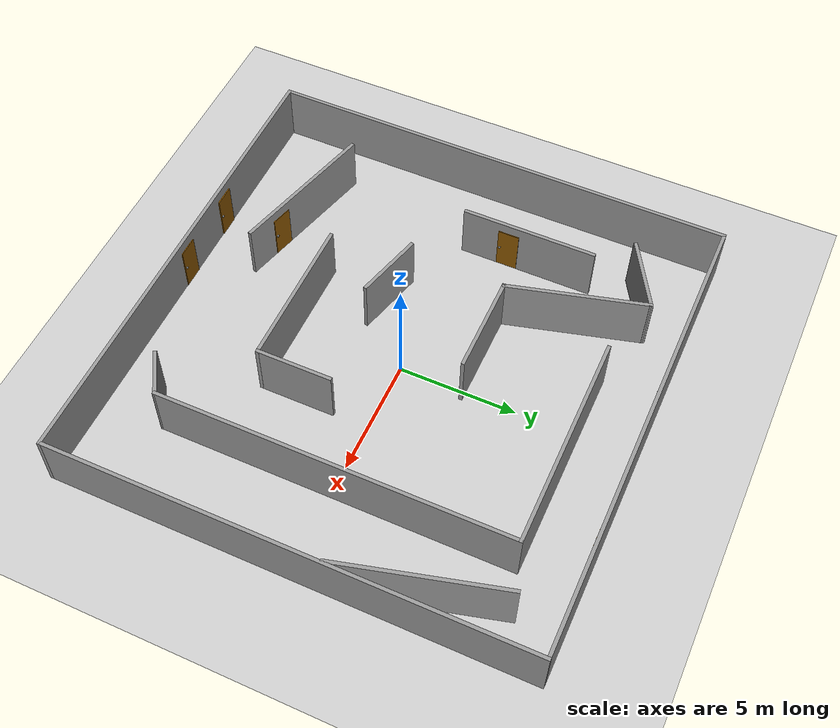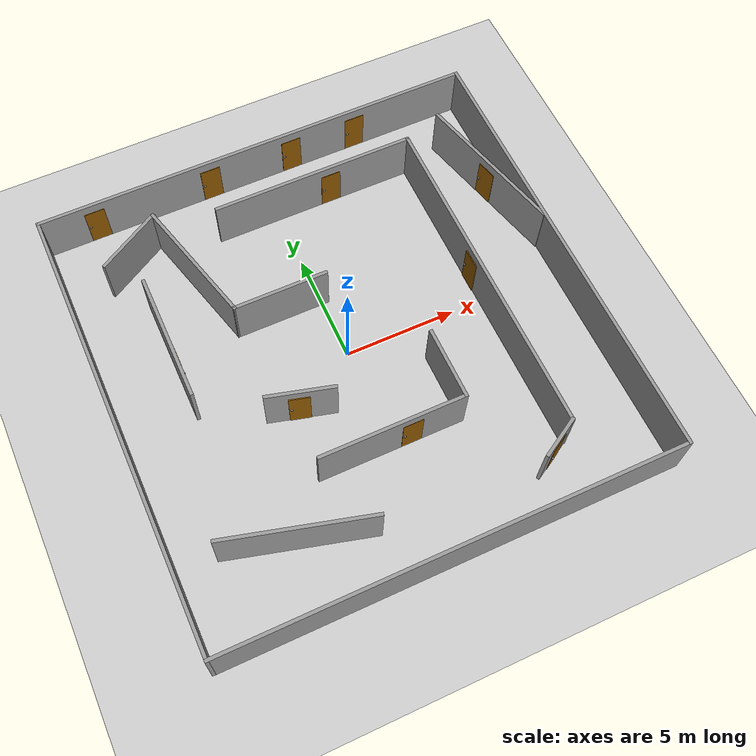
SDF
<sdf version="1.6">
 <world name="default">
  <light name="sun" type="directional">
   <pose>0 0 10 0 -0 0</pose>
   <diffuse>0.8 0.8 0.8 1</diffuse>
   <specular>0.2 0.2 0.2 1</specular>
   <attenuation>
    <range>1000</range>
    <constant>0.9</constant>
    <linear>0.01</linear>
    <quadratic>0.001</quadratic>
   </attenuation>
   <direction>-0.5 0.1 -0.9</direction>
  </light>
  <model name="ground_plane">
   <static>1</static>
   <link name="link">
    <collision name="collision">
     <geometry><plane><normal>0 0 1</normal><size>100 100</size></plane></geometry>
     <surface>
      <contact><collide_bitmask>65535</collide_bitmask></contact>
      <friction><ode><mu>100</mu><mu2>50</mu2></ode></friction>
     </surface>
    </collision>
    <visual name="visual">
     <cast_shadows>0</cast_shadows>
     <geometry><plane><normal>0 0 1</normal><size>100 100</size></plane></geometry>
     <material>
      <script><uri>file://media/materials/scripts/gazebo.material</uri><name>Gazebo/Grey</name></script>
     </material>
    </visual>
   </link>
  </model>
  <gravity>0 0 -9.8</gravity>
  <magnetic_field>6e-06 2.3e-05 -4.2e-05</magnetic_field>
  <atmosphere type="adiabatic"/>
  <physics name="default_physics" default="0" type="ode">
   <max_step_size>0.001</max_step_size>
   <real_time_factor>1</real_time_factor>
   <real_time_update_rate>1000</real_time_update_rate>
  </physics>
  <scene><ambient>0.4 0.4 0.4 1</ambient><background>0.7 0.7 0.7 1</background><shadows>1</shadows></scene>
  <audio><device>default</device></audio>
  <spherical_coordinates>
   <surface_model>EARTH_WGS84</surface_model>
   <latitude_deg>0</latitude_deg>
   <longitude_deg>0</longitude_deg>
   <elevation>0</elevation>
   <heading_deg>0</heading_deg>
  </spherical_coordinates>
  <model name="random">
   <link name="Wall_10">
    <collision name="Wall_10_Collision">
     <geometry><box><size>3 0.15 2.5</size></box></geometry>
     <pose>0 0 1.25 0 -0 0</pose>
    </collision>
    <visual name="Wall_10_Visual">
     <pose>0 0 1.25 0 -0 0</pose>
     <geometry><box><size>3 0.15 2.5</size></box></geometry>
     <material>
      <script><uri>file://media/materials/scripts/gazebo.material</uri><name>Gazebo/Grey</name></script>
      <ambient>1 1 1 1</ambient>
     </material>
     <meta><layer>0</layer></meta>
    </visual>
    <pose>-2.88006 -1.82082 0 0 -0 -0.261799</pose>
   </link>
   <link name="Wall_12">
    <collision name="Wall_12_Collision">
     <geometry><box><size>3.25 0.15 2.5</size></box></geometry>
     <pose>0 0 1.25 0 -0 0</pose>
    </collision>
    <visual name="Wall_12_Visual">
     <pose>0 0 1.25 0 -0 0</pose>
     <geometry><box><size>3.25 0.15 2.5</size></box></geometry>
     <material>
      <script><uri>file://media/materials/scripts/gazebo.material</uri><name>Gazebo/Grey</name></script>
      <ambient>1 1 1 1</ambient>
     </material>
     <meta><layer>0</layer></meta>
    </visual>
    <pose>3.023 -3.1055 0 0 -0 -1.5708</pose>
   </link>
   <link name="Wall_13">
    <collision name="Wall_13_Collision">
     <geometry><box><size>6.5 0.15 2.5</size></box></geometry>
     <pose>0 0 1.25 0 -0 0</pose>
    </collision>
    <visual name="Wall_13_Visual">
     <pose>0 0 1.25 0 -0 0</pose>
     <geometry><box><size>6.5 0.15 2.5</size></box></geometry>
     <material>
      <script><uri>file://media/materials/scripts/gazebo.material</uri><name>Gazebo/Grey</name></script>
      <ambient>1 1 1 1</ambient>
     </material>
     <meta><layer>0</layer></meta>
    </visual>
    <pose>-0.152 -4.6555 0 0 -0 3.14159</pose>
   </link>
   <link name="Wall_15">
    <collision name="Wall_15_Collision">
     <geometry><box><size>5.75 0.15 2.5</size></box></geometry>
     <pose>0 0 1.25 0 -0 0</pose>
    </collision>
    <visual name="Wall_15_Visual">
     <pose>0 0 1.25 0 -0 0</pose>
     <geometry><box><size>5.75 0.15 2.5</size></box></geometry>
     <material>
      <script><uri>file://media/materials/scripts/gazebo.material</uri><name>Gazebo/Grey</name></script>
      <ambient>1 1 1 1</ambient>
     </material>
     <meta><layer>0</layer></meta>
    </visual>
    <pose>-6.8325 2.682 0 0 -0 1.5708</pose>
   </link>
   <link name="Wall_17">
    <collision name="Wall_17_Collision">
     <geometry><box><size>9.25 0.15 2.5</size></box></geometry>
     <pose>0 0 1.25 0 -0 0</pose>
    </collision>
    <visual name="Wall_17_Visual">
     <pose>0 0 1.25 0 -0 0</pose>
     <geometry><box><size>9.25 0.15 2.5</size></box></geometry>
     <material>
      <script><uri>file://media/materials/scripts/gazebo.material</uri><name>Gazebo/Grey</name></script>
      <ambient>1 1 1 1</ambient>
     </material>
     <meta><layer>0</layer></meta>
    </visual>
    <pose>1.7951 7.57362 0 0 -0 0</pose>
   </link>
   <link name="Wall_18">
    <collision name="Wall_18_Collision">
     <geometry><box><size>15 0.15 2.5</size></box></geometry>
     <pose>0 0 1.25 0 -0 0</pose>
    </collision>
    <visual name="Wall_18_Visual">
     <pose>0 0 1.25 0 -0 0</pose>
     <geometry><box><size>15 0.15 2.5</size></box></geometry>
     <material>
      <script><uri>file://media/materials/scripts/gazebo.material</uri><name>Gazebo/Grey</name></script>
      <ambient>1 1 1 1</ambient>
     </material>
     <meta><layer>0</layer></meta>
    </visual>
    <pose>6.3451 0.148619 0 0 -0 -1.5708</pose>
   </link>
   <link name="Wall_19">
    <collision name="Wall_19_Collision">
     <geometry><box><size>2 0.15 2.5</size></box></geometry>
     <pose>0 0 1.25 0 -0 0</pose>
    </collision>
    <visual name="Wall_19_Visual">
     <pose>0 0 1.25 0 -0 0</pose>
     <geometry><box><size>2 0.15 2.5</size></box></geometry>
     <material>
      <script><uri>file://media/materials/scripts/gazebo.material</uri><name>Gazebo/Grey</name></script>
      <ambient>1 1 1 1</ambient>
     </material>
     <meta><layer>0</layer></meta>
    </visual>
    <pose>5.54403 -7.73888 0 0 -0 -2.61799</pose>
   </link>
   <link name="Wall_2">
    <collision name="Wall_2_Collision">
     <geometry><box><size>20.15 0.15 2.5</size></box></geometry>
     <pose>0 0 1.25 0 -0 0</pose>
    </collision>
    <visual name="Wall_2_Visual">
     <pose>0 0 1.25 0 -0 0</pose>
     <geometry><box><size>20.15 0.15 2.5</size></box></geometry>
     <material>
      <script><uri>file://media/materials/scripts/gazebo.material</uri><name>Gazebo/Grey</name></script>
      <ambient>1 1 1 1</ambient>
     </material>
     <meta><layer>0</layer></meta>
    </visual>
    <pose>10 0 0 0 -0 -1.5708</pose>
   </link>
   <link name="Wall_21">
    <collision name="Wall_21_Collision">
     <geometry><box><size>4.25 0.15 2.5</size></box></geometry>
     <pose>0 0 1.25 0 -0 0</pose>
    </collision>
    <visual name="Wall_21_Visual">
     <pose>0 0 1.25 0 -0 0</pose>
     <geometry><box><size>4.25 0.15 2.5</size></box></geometry>
     <material>
      <script><uri>file://media/materials/scripts/gazebo.material</uri><name>Gazebo/Grey</name></script>
      <ambient>1 1 1 1</ambient>
     </material>
     <meta><layer>0</layer></meta>
    </visual>
    <pose>-1.81119 2.75941 0 0 -0 3.14159</pose>
   </link>
   <link name="Wall_22">
    <collision name="Wall_22_Collision">
     <geometry><box><size>6 0.15 2.5</size></box></geometry>
     <pose>0 0 1.25 0 -0 0</pose>
    </collision>
    <visual name="Wall_22_Visual">
     <pose>0 0 1.25 0 -0 0</pose>
     <geometry><box><size>6 0.15 2.5</size></box></geometry>
     <material>
      <script><uri>file://media/materials/scripts/gazebo.material</uri><name>Gazebo/Grey</name></script>
      <ambient>1 1 1 1</ambient>
     </material>
     <meta><layer>0</layer></meta>
    </visual>
    <pose>-4.61823 5.58474 0 0 -0 1.8326</pose>
   </link>
   <link name="Wall_23">
    <collision name="Wall_23_Collision">
     <geometry><box><size>3.25 0.15 2.5</size></box></geometry>
     <pose>0 0 1.25 0 -0 0</pose>
    </collision>
    <visual name="Wall_23_Visual">
     <pose>0 0 1.25 0 -0 0</pose>
     <geometry><box><size>3.25 0.15 2.5</size></box></geometry>
     <material>
      <script><uri>file://media/materials/scripts/gazebo.material</uri><name>Gazebo/Grey</name></script>
      <ambient>1 1 1 1</ambient>
     </material>
     <meta><layer>0</layer></meta>
    </visual>
    <pose>-6.71762 7.63507 0 0 -0 -2.61799</pose>
   </link>
   <link name="Wall_25">
    <collision name="Wall_25_Collision">
     <geometry><box><size>6.5 0.15 2.5</size></box></geometry>
     <pose>0 0 1.25 0 -0 0</pose>
    </collision>
    <visual name="Wall_25_Visual">
     <pose>0 0 1.25 0 -0 0</pose>
     <geometry><box><size>6.5 0.15 2.5</size></box></geometry>
     <material>
      <script><uri>file://media/materials/scripts/gazebo.material</uri><name>Gazebo/Grey</name></script>
      <ambient>1 1 1 1</ambient>
     </material>
     <meta><layer>0</layer></meta>
    </visual>
    <pose>-5.14959 -6.88166 0 0 -0 -0.261799</pose>
   </link>
   <link name="Wall_27">
    <collision name="Wall_27_Collision">
     <geometry><box><size>7 0.15 2.5</size></box></geometry>
     <pose>0 0 1.25 0 -0 0</pose>
    </collision>
    <visual name="Wall_27_Visual">
     <pose>0 0 1.25 0 -0 0</pose>
     <geometry><box><size>7 0.15 2.5</size></box></geometry>
     <material>
      <script><uri>file://media/materials/scripts/gazebo.material</uri><name>Gazebo/Grey</name></script>
      <ambient>1 1 1 1</ambient>
     </material>
     <meta><layer>0</layer></meta>
    </visual>
    <pose>9.05456 4.87216 0 0 -0 -1.309</pose>
   </link>
   <link name="Wall_4">
    <collision name="Wall_4_Collision">
     <geometry><box><size>20.15 0.15 2.5</size></box></geometry>
     <pose>0 0 1.25 0 -0 0</pose>
    </collision>
    <visual name="Wall_4_Visual">
     <pose>0 0 1.25 0 -0 0</pose>
     <geometry><box><size>20.15 0.15 2.5</size></box></geometry>
     <material>
      <script><uri>file://media/materials/scripts/gazebo.material</uri><name>Gazebo/Grey</name></script>
      <ambient>1 1 1 1</ambient>
     </material>
     <meta><layer>0</layer></meta>
    </visual>
    <pose>0 10 0 0 -0 3.14159</pose>
   </link>
   <link name="Wall_6">
    <collision name="Wall_6_Collision">
     <geometry><box><size>20.15 0.15 2.5</size></box></geometry>
     <pose>0 0 1.25 0 -0 0</pose>
    </collision>
    <visual name="Wall_6_Visual">
     <pose>0 0 1.25 0 -0 0</pose>
     <geometry><box><size>20.15 0.15 2.5</size></box></geometry>
     <material>
      <script><uri>file://media/materials/scripts/gazebo.material</uri><name>Gazebo/Grey</name></script>
      <ambient>1 1 1 1</ambient>
     </material>
     <meta><layer>0</layer></meta>
    </visual>
    <pose>0 -10 0 0 -0 3.14159</pose>
   </link>
   <link name="Wall_8">
    <collision name="Wall_8_Collision">
     <geometry><box><size>20.15 0.15 2.5</size></box></geometry>
     <pose>0 0 1.25 0 -0 0</pose>
    </collision>
    <visual name="Wall_8_Visual">
     <pose>0 0 1.25 0 -0 0</pose>
     <geometry><box><size>20.15 0.15 2.5</size></box></geometry>
     <material>
      <script><uri>file://media/materials/scripts/gazebo.material</uri><name>Gazebo/Grey</name></script>
      <ambient>1 1 1 1</ambient>
     </material>
     <meta><layer>0</layer></meta>
    </visual>
    <pose>-10 0 0 0 -0 -1.5708</pose>
   </link>
   <static>1</static>
  </model>
  <model name="custom_door">
   <link name="link_0">
    <inertial>
     <mass>1</mass>
     <inertia>
      <ixx>0.166667</ixx>
      <ixy>0</ixy>
      <ixz>0</ixz>
      <iyy>0.166667</iyy>
      <iyz>0</iyz>
      <izz>0.166667</izz>
     </inertia>
    </inertial>
    <pose>0.023443 -0.170637 -0.020383 0 -0 0</pose>
    <visual name="visual">
     <geometry><box><size>0.05 0.9 2</size></box></geometry>
     <material>
      <lighting>1</lighting>
      <script><uri>file://media/materials/scripts/gazebo.material</uri><name>Gazebo/Grey</name></script>
      <shader type="vertex"><normal_map>__default__</normal_map></shader>
      <ambient>0.561 0.349 0.008 1</ambient>
      <diffuse>0.561 0.349 0.008 1</diffuse>
      <specular>0.561 0.349 0.008 1</specular>
      <emissive>0 0 0 1</emissive>
     </material>
    </visual>
    <collision name="collision">
     <geometry><box><size>0.05 0.9 2</size></box></geometry>
     <surface>
      <friction>
       <ode><mu>1</mu><mu2>1</mu2><fdir1>0 0 0</fdir1><slip1>0</slip1><slip2>0</slip2></ode>
       <torsional>
        <coefficient>1</coefficient>
        <patch_radius>0</patch_radius>
        <surface_radius>0</surface_radius>
        <use_patch_radius>1</use_patch_radius>
        <ode><slip>0</slip></ode>
       </torsional>
      </friction>
      <bounce><restitution_coefficient>0</restitution_coefficient><threshold>1e+06</threshold></bounce>
      <contact>
       <collide_without_contact>0</collide_without_contact>
       <collide_without_contact_bitmask>1</collide_without_contact_bitmask>
       <collide_bitmask>1</collide_bitmask>
       <ode>
        <soft_cfm>0</soft_cfm>
        <soft_erp>0.2</soft_erp>
        <kp>1e+13</kp>
        <kd>1</kd>
        <max_vel>0.01</max_vel>
        <min_depth>0</min_depth>
       </ode>
       <bullet>
        <split_impulse>1</split_impulse>
        <split_impulse_penetration_threshold>-0.01</split_impulse_penetration_threshold>
        <soft_cfm>0</soft_cfm>
        <soft_erp>0.2</soft_erp>
        <kp>1e+13</kp>
        <kd>1</kd>
       </bullet>
      </contact>
     </surface>
    </collision>
   </link>
   <link name="link_1">
    <inertial>
     <mass>1</mass>
     <inertia><ixx>0.1</ixx><ixy>0</ixy><ixz>0</ixz><iyy>0.1</iyy><iyz>0</iyz><izz>0.1</izz></inertia>
    </inertial>
    <pose>-0.023443 0.170636 0.020383 0 -0 0</pose>
    <gravity>0</gravity>
    <visual name="visual">
     <geometry><sphere><radius>0.05</radius></sphere></geometry>
     <material>
      <lighting>1</lighting>
      <script><uri>file://media/materials/scripts/gazebo.material</uri><name>Gazebo/Grey</name></script>
      <shader type="vertex"><normal_map>__default__</normal_map></shader>
      <ambient>0.729 0.741 0.714 1</ambient>
      <diffuse>0.729 0.741 0.714 1</diffuse>
      <specular>0.729 0.741 0.714 1</specular>
      <emissive>0 0 0 1</emissive>
     </material>
    </visual>
    <collision name="collision">
     <geometry><sphere><radius>0.05</radius></sphere></geometry>
     <surface>
      <friction>
       <ode><mu>1</mu><mu2>1</mu2><fdir1>0 0 0</fdir1><slip1>0</slip1><slip2>0</slip2></ode>
       <torsional>
        <coefficient>1</coefficient>
        <patch_radius>0</patch_radius>
        <surface_radius>0</surface_radius>
        <use_patch_radius>1</use_patch_radius>
        <ode><slip>0</slip></ode>
       </torsional>
      </friction>
      <bounce><restitution_coefficient>0</restitution_coefficient><threshold>1e+06</threshold></bounce>
      <contact>
       <collide_without_contact>0</collide_without_contact>
       <collide_without_contact_bitmask>1</collide_without_contact_bitmask>
       <collide_bitmask>1</collide_bitmask>
       <ode>
        <soft_cfm>0</soft_cfm>
        <soft_erp>0.2</soft_erp>
        <kp>1e+13</kp>
        <kd>1</kd>
        <max_vel>0.01</max_vel>
        <min_depth>0</min_depth>
       </ode>
       <bullet>
        <split_impulse>1</split_impulse>
        <split_impulse_penetration_threshold>-0.01</split_impulse_penetration_threshold>
        <soft_cfm>0</soft_cfm>
        <soft_erp>0.2</soft_erp>
        <kp>1e+13</kp>
        <kd>1</kd>
       </bullet>
      </contact>
     </surface>
    </collision>
   </link>
   <joint name="link_0_JOINT_0" type="fixed">
    <parent>link_0</parent>
    <child>link_1</child>
    <physics>
     <ode><limit><cfm>0</cfm><erp>0.2</erp></limit><suspension><cfm>0</cfm><erp>0.2</erp></suspension></ode>
    </physics>
   </joint>
   <static>1</static>
   <pose>6.22853 1.23909 1.06 0 -0 0</pose>
  </model>
  <model name="custom_door_0">
   <link name="link_0">
    <inertial>
     <mass>1</mass>
     <inertia>
      <ixx>0.166667</ixx>
      <ixy>0</ixy>
      <ixz>0</ixz>
      <iyy>0.166667</iyy>
      <iyz>0</iyz>
      <izz>0.166667</izz>
     </inertia>
    </inertial>
    <pose>0.023443 -0.170637 -0.020383 0 -0 0</pose>
    <visual name="visual">
     <geometry><box><size>0.05 0.9 2</size></box></geometry>
     <material>
      <lighting>1</lighting>
      <script><uri>file://media/materials/scripts/gazebo.material</uri><name>Gazebo/Grey</name></script>
      <shader type="vertex"><normal_map>__default__</normal_map></shader>
      <ambient>0.561 0.349 0.008 1</ambient>
      <diffuse>0.561 0.349 0.008 1</diffuse>
      <specular>0.561 0.349 0.008 1</specular>
      <emissive>0 0 0 1</emissive>
     </material>
    </visual>
    <collision name="collision">
     <geometry><box><size>0.05 0.9 2</size></box></geometry>
     <surface>
      <friction>
       <ode><mu>1</mu><mu2>1</mu2><fdir1>0 0 0</fdir1><slip1>0</slip1><slip2>0</slip2></ode>
       <torsional>
        <coefficient>1</coefficient>
        <patch_radius>0</patch_radius>
        <surface_radius>0</surface_radius>
        <use_patch_radius>1</use_patch_radius>
        <ode><slip>0</slip></ode>
       </torsional>
      </friction>
      <bounce><restitution_coefficient>0</restitution_coefficient><threshold>1e+06</threshold></bounce>
      <contact>
       <collide_without_contact>0</collide_without_contact>
       <collide_without_contact_bitmask>1</collide_without_contact_bitmask>
       <collide_bitmask>1</collide_bitmask>
       <ode>
        <soft_cfm>0</soft_cfm>
        <soft_erp>0.2</soft_erp>
        <kp>1e+13</kp>
        <kd>1</kd>
        <max_vel>0.01</max_vel>
        <min_depth>0</min_depth>
       </ode>
       <bullet>
        <split_impulse>1</split_impulse>
        <split_impulse_penetration_threshold>-0.01</split_impulse_penetration_threshold>
        <soft_cfm>0</soft_cfm>
        <soft_erp>0.2</soft_erp>
        <kp>1e+13</kp>
        <kd>1</kd>
       </bullet>
      </contact>
     </surface>
    </collision>
   </link>
   <link name="link_1">
    <inertial>
     <mass>1</mass>
     <inertia><ixx>0.1</ixx><ixy>0</ixy><ixz>0</ixz><iyy>0.1</iyy><iyz>0</iyz><izz>0.1</izz></inertia>
    </inertial>
    <pose>-0.023443 0.170636 0.020383 0 -0 0</pose>
    <gravity>0</gravity>
    <visual name="visual">
     <geometry><sphere><radius>0.05</radius></sphere></geometry>
     <material>
      <lighting>1</lighting>
      <script><uri>file://media/materials/scripts/gazebo.material</uri><name>Gazebo/Grey</name></script>
      <shader type="vertex"><normal_map>__default__</normal_map></shader>
      <ambient>0.729 0.741 0.714 1</ambient>
      <diffuse>0.729 0.741 0.714 1</diffuse>
      <specular>0.729 0.741 0.714 1</specular>
      <emissive>0 0 0 1</emissive>
     </material>
    </visual>
    <collision name="collision">
     <geometry><sphere><radius>0.05</radius></sphere></geometry>
     <surface>
      <friction>
       <ode><mu>1</mu><mu2>1</mu2><fdir1>0 0 0</fdir1><slip1>0</slip1><slip2>0</slip2></ode>
       <torsional>
        <coefficient>1</coefficient>
        <patch_radius>0</patch_radius>
        <surface_radius>0</surface_radius>
        <use_patch_radius>1</use_patch_radius>
        <ode><slip>0</slip></ode>
       </torsional>
      </friction>
      <bounce><restitution_coefficient>0</restitution_coefficient><threshold>1e+06</threshold></bounce>
      <contact>
       <collide_without_contact>0</collide_without_contact>
       <collide_without_contact_bitmask>1</collide_without_contact_bitmask>
       <collide_bitmask>1</collide_bitmask>
       <ode>
        <soft_cfm>0</soft_cfm>
        <soft_erp>0.2</soft_erp>
        <kp>1e+13</kp>
        <kd>1</kd>
        <max_vel>0.01</max_vel>
        <min_depth>0</min_depth>
       </ode>
       <bullet>
        <split_impulse>1</split_impulse>
        <split_impulse_penetration_threshold>-0.01</split_impulse_penetration_threshold>
        <soft_cfm>0</soft_cfm>
        <soft_erp>0.2</soft_erp>
        <kp>1e+13</kp>
        <kd>1</kd>
       </bullet>
      </contact>
     </surface>
    </collision>
   </link>
   <joint name="link_0_JOINT_0" type="fixed">
    <parent>link_0</parent>
    <child>link_1</child>
    <physics>
     <ode><limit><cfm>0</cfm><erp>0.2</erp></limit><suspension><cfm>0</cfm><erp>0.2</erp></suspension></ode>
    </physics>
   </joint>
   <static>1</static>
   <pose>2.38783 7.47226 1.06 0 -0 1.5708</pose>
  </model>
  <model name="custom_door_1">
   <link name="link_0">
    <inertial>
     <mass>1</mass>
     <inertia>
      <ixx>0.166667</ixx>
      <ixy>0</ixy>
      <ixz>0</ixz>
      <iyy>0.166667</iyy>
      <iyz>0</iyz>
      <izz>0.166667</izz>
     </inertia>
    </inertial>
    <pose>0.023443 -0.170637 -0.020383 0 -0 0</pose>
    <visual name="visual">
     <geometry><box><size>0.05 0.9 2</size></box></geometry>
     <material>
      <lighting>1</lighting>
      <script><uri>file://media/materials/scripts/gazebo.material</uri><name>Gazebo/Grey</name></script>
      <shader type="vertex"><normal_map>__default__</normal_map></shader>
      <ambient>0.561 0.349 0.008 1</ambient>
      <diffuse>0.561 0.349 0.008 1</diffuse>
      <specular>0.561 0.349 0.008 1</specular>
      <emissive>0 0 0 1</emissive>
     </material>
    </visual>
    <collision name="collision">
     <geometry><box><size>0.05 0.9 2</size></box></geometry>
     <surface>
      <friction>
       <ode><mu>1</mu><mu2>1</mu2><fdir1>0 0 0</fdir1><slip1>0</slip1><slip2>0</slip2></ode>
       <torsional>
        <coefficient>1</coefficient>
        <patch_radius>0</patch_radius>
        <surface_radius>0</surface_radius>
        <use_patch_radius>1</use_patch_radius>
        <ode><slip>0</slip></ode>
       </torsional>
      </friction>
      <bounce><restitution_coefficient>0</restitution_coefficient><threshold>1e+06</threshold></bounce>
      <contact>
       <collide_without_contact>0</collide_without_contact>
       <collide_without_contact_bitmask>1</collide_without_contact_bitmask>
       <collide_bitmask>1</collide_bitmask>
       <ode>
        <soft_cfm>0</soft_cfm>
        <soft_erp>0.2</soft_erp>
        <kp>1e+13</kp>
        <kd>1</kd>
        <max_vel>0.01</max_vel>
        <min_depth>0</min_depth>
       </ode>
       <bullet>
        <split_impulse>1</split_impulse>
        <split_impulse_penetration_threshold>-0.01</split_impulse_penetration_threshold>
        <soft_cfm>0</soft_cfm>
        <soft_erp>0.2</soft_erp>
        <kp>1e+13</kp>
        <kd>1</kd>
       </bullet>
      </contact>
     </surface>
    </collision>
   </link>
   <link name="link_1">
    <inertial>
     <mass>1</mass>
     <inertia><ixx>0.1</ixx><ixy>0</ixy><ixz>0</ixz><iyy>0.1</iyy><iyz>0</iyz><izz>0.1</izz></inertia>
    </inertial>
    <pose>-0.023443 0.170636 0.020383 0 -0 0</pose>
    <gravity>0</gravity>
    <visual name="visual">
     <geometry><sphere><radius>0.05</radius></sphere></geometry>
     <material>
      <lighting>1</lighting>
      <script><uri>file://media/materials/scripts/gazebo.material</uri><name>Gazebo/Grey</name></script>
      <shader type="vertex"><normal_map>__default__</normal_map></shader>
      <ambient>0.729 0.741 0.714 1</ambient>
      <diffuse>0.729 0.741 0.714 1</diffuse>
      <specular>0.729 0.741 0.714 1</specular>
      <emissive>0 0 0 1</emissive>
     </material>
    </visual>
    <collision name="collision">
     <geometry><sphere><radius>0.05</radius></sphere></geometry>
     <surface>
      <friction>
       <ode><mu>1</mu><mu2>1</mu2><fdir1>0 0 0</fdir1><slip1>0</slip1><slip2>0</slip2></ode>
       <torsional>
        <coefficient>1</coefficient>
        <patch_radius>0</patch_radius>
        <surface_radius>0</surface_radius>
        <use_patch_radius>1</use_patch_radius>
        <ode><slip>0</slip></ode>
       </torsional>
      </friction>
      <bounce><restitution_coefficient>0</restitution_coefficient><threshold>1e+06</threshold></bounce>
      <contact>
       <collide_without_contact>0</collide_without_contact>
       <collide_without_contact_bitmask>1</collide_without_contact_bitmask>
       <collide_bitmask>1</collide_bitmask>
       <ode>
        <soft_cfm>0</soft_cfm>
        <soft_erp>0.2</soft_erp>
        <kp>1e+13</kp>
        <kd>1</kd>
        <max_vel>0.01</max_vel>
        <min_depth>0</min_depth>
       </ode>
       <bullet>
        <split_impulse>1</split_impulse>
        <split_impulse_penetration_threshold>-0.01</split_impulse_penetration_threshold>
        <soft_cfm>0</soft_cfm>
        <soft_erp>0.2</soft_erp>
        <kp>1e+13</kp>
        <kd>1</kd>
       </bullet>
      </contact>
     </surface>
    </collision>
   </link>
   <joint name="link_0_JOINT_0" type="fixed">
    <parent>link_0</parent>
    <child>link_1</child>
    <physics>
     <ode><limit><cfm>0</cfm><erp>0.2</erp></limit><suspension><cfm>0</cfm><erp>0.2</erp></suspension></ode>
    </physics>
   </joint>
   <static>1</static>
   <pose>-3.14628 -1.86988 1.06 0 -0 1.31512</pose>
  </model>
  <model name="custom_door_2">
   <link name="link_0">
    <inertial>
     <mass>1</mass>
     <inertia>
      <ixx>0.166667</ixx>
      <ixy>0</ixy>
      <ixz>0</ixz>
      <iyy>0.166667</iyy>
      <iyz>0</iyz>
      <izz>0.166667</izz>
     </inertia>
    </inertial>
    <pose>0.023443 -0.170637 -0.020383 0 -0 0</pose>
    <visual name="visual">
     <geometry><box><size>0.05 0.9 2</size></box></geometry>
     <material>
      <lighting>1</lighting>
      <script><uri>file://media/materials/scripts/gazebo.material</uri><name>Gazebo/Grey</name></script>
      <shader type="vertex"><normal_map>__default__</normal_map></shader>
      <ambient>0.561 0.349 0.008 1</ambient>
      <diffuse>0.561 0.349 0.008 1</diffuse>
      <specular>0.561 0.349 0.008 1</specular>
      <emissive>0 0 0 1</emissive>
     </material>
    </visual>
    <collision name="collision">
     <geometry><box><size>0.05 0.9 2</size></box></geometry>
     <surface>
      <friction>
       <ode><mu>1</mu><mu2>1</mu2><fdir1>0 0 0</fdir1><slip1>0</slip1><slip2>0</slip2></ode>
       <torsional>
        <coefficient>1</coefficient>
        <patch_radius>0</patch_radius>
        <surface_radius>0</surface_radius>
        <use_patch_radius>1</use_patch_radius>
        <ode><slip>0</slip></ode>
       </torsional>
      </friction>
      <bounce><restitution_coefficient>0</restitution_coefficient><threshold>1e+06</threshold></bounce>
      <contact>
       <collide_without_contact>0</collide_without_contact>
       <collide_without_contact_bitmask>1</collide_without_contact_bitmask>
       <collide_bitmask>1</collide_bitmask>
       <ode>
        <soft_cfm>0</soft_cfm>
        <soft_erp>0.2</soft_erp>
        <kp>1e+13</kp>
        <kd>1</kd>
        <max_vel>0.01</max_vel>
        <min_depth>0</min_depth>
       </ode>
       <bullet>
        <split_impulse>1</split_impulse>
        <split_impulse_penetration_threshold>-0.01</split_impulse_penetration_threshold>
        <soft_cfm>0</soft_cfm>
        <soft_erp>0.2</soft_erp>
        <kp>1e+13</kp>
        <kd>1</kd>
       </bullet>
      </contact>
     </surface>
    </collision>
   </link>
   <link name="link_1">
    <inertial>
     <mass>1</mass>
     <inertia><ixx>0.1</ixx><ixy>0</ixy><ixz>0</ixz><iyy>0.1</iyy><iyz>0</iyz><izz>0.1</izz></inertia>
    </inertial>
    <pose>-0.023443 0.170636 0.020383 0 -0 0</pose>
    <gravity>0</gravity>
    <visual name="visual">
     <geometry><sphere><radius>0.05</radius></sphere></geometry>
     <material>
      <lighting>1</lighting>
      <script><uri>file://media/materials/scripts/gazebo.material</uri><name>Gazebo/Grey</name></script>
      <shader type="vertex"><normal_map>__default__</normal_map></shader>
      <ambient>0.729 0.741 0.714 1</ambient>
      <diffuse>0.729 0.741 0.714 1</diffuse>
      <specular>0.729 0.741 0.714 1</specular>
      <emissive>0 0 0 1</emissive>
     </material>
    </visual>
    <collision name="collision">
     <geometry><sphere><radius>0.05</radius></sphere></geometry>
     <surface>
      <friction>
       <ode><mu>1</mu><mu2>1</mu2><fdir1>0 0 0</fdir1><slip1>0</slip1><slip2>0</slip2></ode>
       <torsional>
        <coefficient>1</coefficient>
        <patch_radius>0</patch_radius>
        <surface_radius>0</surface_radius>
        <use_patch_radius>1</use_patch_radius>
        <ode><slip>0</slip></ode>
       </torsional>
      </friction>
      <bounce><restitution_coefficient>0</restitution_coefficient><threshold>1e+06</threshold></bounce>
      <contact>
       <collide_without_contact>0</collide_without_contact>
       <collide_without_contact_bitmask>1</collide_without_contact_bitmask>
       <collide_bitmask>1</collide_bitmask>
       <ode>
        <soft_cfm>0</soft_cfm>
        <soft_erp>0.2</soft_erp>
        <kp>1e+13</kp>
        <kd>1</kd>
        <max_vel>0.01</max_vel>
        <min_depth>0</min_depth>
       </ode>
       <bullet>
        <split_impulse>1</split_impulse>
        <split_impulse_penetration_threshold>-0.01</split_impulse_penetration_threshold>
        <soft_cfm>0</soft_cfm>
        <soft_erp>0.2</soft_erp>
        <kp>1e+13</kp>
        <kd>1</kd>
       </bullet>
      </contact>
     </surface>
    </collision>
   </link>
   <joint name="link_0_JOINT_0" type="fixed">
    <parent>link_0</parent>
    <child>link_1</child>
    <physics>
     <ode><limit><cfm>0</cfm><erp>0.2</erp></limit><suspension><cfm>0</cfm><erp>0.2</erp></suspension></ode>
    </physics>
   </joint>
   <static>1</static>
   <pose>-6.72838 1.67708 1.06 0 -0 3.14159</pose>
  </model>
  <model name="custom_door_3">
   <link name="link_0">
    <inertial>
     <mass>1</mass>
     <inertia>
      <ixx>0.166667</ixx>
      <ixy>0</ixy>
      <ixz>0</ixz>
      <iyy>0.166667</iyy>
      <iyz>0</iyz>
      <izz>0.166667</izz>
     </inertia>
    </inertial>
    <pose>0.023443 -0.170637 -0.020383 0 -0 0</pose>
    <visual name="visual">
     <geometry><box><size>0.05 0.9 2</size></box></geometry>
     <material>
      <lighting>1</lighting>
      <script><uri>file://media/materials/scripts/gazebo.material</uri><name>Gazebo/Grey</name></script>
      <shader type="vertex"><normal_map>__default__</normal_map></shader>
      <ambient>0.561 0.349 0.008 1</ambient>
      <diffuse>0.561 0.349 0.008 1</diffuse>
      <specular>0.561 0.349 0.008 1</specular>
      <emissive>0 0 0 1</emissive>
     </material>
    </visual>
    <collision name="collision">
     <geometry><box><size>0.05 0.9 2</size></box></geometry>
     <surface>
      <friction>
       <ode><mu>1</mu><mu2>1</mu2><fdir1>0 0 0</fdir1><slip1>0</slip1><slip2>0</slip2></ode>
       <torsional>
        <coefficient>1</coefficient>
        <patch_radius>0</patch_radius>
        <surface_radius>0</surface_radius>
        <use_patch_radius>1</use_patch_radius>
        <ode><slip>0</slip></ode>
       </torsional>
      </friction>
      <bounce><restitution_coefficient>0</restitution_coefficient><threshold>1e+06</threshold></bounce>
      <contact>
       <collide_without_contact>0</collide_without_contact>
       <collide_without_contact_bitmask>1</collide_without_contact_bitmask>
       <collide_bitmask>1</collide_bitmask>
       <ode>
        <soft_cfm>0</soft_cfm>
        <soft_erp>0.2</soft_erp>
        <kp>1e+13</kp>
        <kd>1</kd>
        <max_vel>0.01</max_vel>
        <min_depth>0</min_depth>
       </ode>
       <bullet>
        <split_impulse>1</split_impulse>
        <split_impulse_penetration_threshold>-0.01</split_impulse_penetration_threshold>
        <soft_cfm>0</soft_cfm>
        <soft_erp>0.2</soft_erp>
        <kp>1e+13</kp>
        <kd>1</kd>
       </bullet>
      </contact>
     </surface>
    </collision>
   </link>
   <link name="link_1">
    <inertial>
     <mass>1</mass>
     <inertia><ixx>0.1</ixx><ixy>0</ixy><ixz>0</ixz><iyy>0.1</iyy><iyz>0</iyz><izz>0.1</izz></inertia>
    </inertial>
    <pose>-0.023443 0.170636 0.020383 0 -0 0</pose>
    <gravity>0</gravity>
    <visual name="visual">
     <geometry><sphere><radius>0.05</radius></sphere></geometry>
     <material>
      <lighting>1</lighting>
      <script><uri>file://media/materials/scripts/gazebo.material</uri><name>Gazebo/Grey</name></script>
      <shader type="vertex"><normal_map>__default__</normal_map></shader>
      <ambient>0.729 0.741 0.714 1</ambient>
      <diffuse>0.729 0.741 0.714 1</diffuse>
      <specular>0.729 0.741 0.714 1</specular>
      <emissive>0 0 0 1</emissive>
     </material>
    </visual>
    <collision name="collision">
     <geometry><sphere><radius>0.05</radius></sphere></geometry>
     <surface>
      <friction>
       <ode><mu>1</mu><mu2>1</mu2><fdir1>0 0 0</fdir1><slip1>0</slip1><slip2>0</slip2></ode>
       <torsional>
        <coefficient>1</coefficient>
        <patch_radius>0</patch_radius>
        <surface_radius>0</surface_radius>
        <use_patch_radius>1</use_patch_radius>
        <ode><slip>0</slip></ode>
       </torsional>
      </friction>
      <bounce><restitution_coefficient>0</restitution_coefficient><threshold>1e+06</threshold></bounce>
      <contact>
       <collide_without_contact>0</collide_without_contact>
       <collide_without_contact_bitmask>1</collide_without_contact_bitmask>
       <collide_bitmask>1</collide_bitmask>
       <ode>
        <soft_cfm>0</soft_cfm>
        <soft_erp>0.2</soft_erp>
        <kp>1e+13</kp>
        <kd>1</kd>
        <max_vel>0.01</max_vel>
        <min_depth>0</min_depth>
       </ode>
       <bullet>
        <split_impulse>1</split_impulse>
        <split_impulse_penetration_threshold>-0.01</split_impulse_penetration_threshold>
        <soft_cfm>0</soft_cfm>
        <soft_erp>0.2</soft_erp>
        <kp>1e+13</kp>
        <kd>1</kd>
       </bullet>
      </contact>
     </surface>
    </collision>
   </link>
   <joint name="link_0_JOINT_0" type="fixed">
    <parent>link_0</parent>
    <child>link_1</child>
    <physics>
     <ode><limit><cfm>0</cfm><erp>0.2</erp></limit><suspension><cfm>0</cfm><erp>0.2</erp></suspension></ode>
    </physics>
   </joint>
   <static>1</static>
   <pose>-7.77046 9.90053 1.06 0 -0 1.5708</pose>
  </model>
  <model name="custom_door_4">
   <link name="link_0">
    <inertial>
     <mass>1</mass>
     <inertia>
      <ixx>0.166667</ixx>
      <ixy>0</ixy>
      <ixz>0</ixz>
      <iyy>0.166667</iyy>
      <iyz>0</iyz>
      <izz>0.166667</izz>
     </inertia>
    </inertial>
    <pose>0.023443 -0.170637 -0.020383 0 -0 0</pose>
    <visual name="visual">
     <geometry><box><size>0.05 0.9 2</size></box></geometry>
     <material>
      <lighting>1</lighting>
      <script><uri>file://media/materials/scripts/gazebo.material</uri><name>Gazebo/Grey</name></script>
      <shader type="vertex"><normal_map>__default__</normal_map></shader>
      <ambient>0.561 0.349 0.008 1</ambient>
      <diffuse>0.561 0.349 0.008 1</diffuse>
      <specular>0.561 0.349 0.008 1</specular>
      <emissive>0 0 0 1</emissive>
     </material>
    </visual>
    <collision name="collision">
     <geometry><box><size>0.05 0.9 2</size></box></geometry>
     <surface>
      <friction>
       <ode><mu>1</mu><mu2>1</mu2><fdir1>0 0 0</fdir1><slip1>0</slip1><slip2>0</slip2></ode>
       <torsional>
        <coefficient>1</coefficient>
        <patch_radius>0</patch_radius>
        <surface_radius>0</surface_radius>
        <use_patch_radius>1</use_patch_radius>
        <ode><slip>0</slip></ode>
       </torsional>
      </friction>
      <bounce><restitution_coefficient>0</restitution_coefficient><threshold>1e+06</threshold></bounce>
      <contact>
       <collide_without_contact>0</collide_without_contact>
       <collide_without_contact_bitmask>1</collide_without_contact_bitmask>
       <collide_bitmask>1</collide_bitmask>
       <ode>
        <soft_cfm>0</soft_cfm>
        <soft_erp>0.2</soft_erp>
        <kp>1e+13</kp>
        <kd>1</kd>
        <max_vel>0.01</max_vel>
        <min_depth>0</min_depth>
       </ode>
       <bullet>
        <split_impulse>1</split_impulse>
        <split_impulse_penetration_threshold>-0.01</split_impulse_penetration_threshold>
        <soft_cfm>0</soft_cfm>
        <soft_erp>0.2</soft_erp>
        <kp>1e+13</kp>
        <kd>1</kd>
       </bullet>
      </contact>
     </surface>
    </collision>
   </link>
   <link name="link_1">
    <inertial>
     <mass>1</mass>
     <inertia><ixx>0.1</ixx><ixy>0</ixy><ixz>0</ixz><iyy>0.1</iyy><iyz>0</iyz><izz>0.1</izz></inertia>
    </inertial>
    <pose>-0.023443 0.170636 0.020383 0 -0 0</pose>
    <gravity>0</gravity>
    <visual name="visual">
     <geometry><sphere><radius>0.05</radius></sphere></geometry>
     <material>
      <lighting>1</lighting>
      <script><uri>file://media/materials/scripts/gazebo.material</uri><name>Gazebo/Grey</name></script>
      <shader type="vertex"><normal_map>__default__</normal_map></shader>
      <ambient>0.729 0.741 0.714 1</ambient>
      <diffuse>0.729 0.741 0.714 1</diffuse>
      <specular>0.729 0.741 0.714 1</specular>
      <emissive>0 0 0 1</emissive>
     </material>
    </visual>
    <collision name="collision">
     <geometry><sphere><radius>0.05</radius></sphere></geometry>
     <surface>
      <friction>
       <ode><mu>1</mu><mu2>1</mu2><fdir1>0 0 0</fdir1><slip1>0</slip1><slip2>0</slip2></ode>
       <torsional>
        <coefficient>1</coefficient>
        <patch_radius>0</patch_radius>
        <surface_radius>0</surface_radius>
        <use_patch_radius>1</use_patch_radius>
        <ode><slip>0</slip></ode>
       </torsional>
      </friction>
      <bounce><restitution_coefficient>0</restitution_coefficient><threshold>1e+06</threshold></bounce>
      <contact>
       <collide_without_contact>0</collide_without_contact>
       <collide_without_contact_bitmask>1</collide_without_contact_bitmask>
       <collide_bitmask>1</collide_bitmask>
       <ode>
        <soft_cfm>0</soft_cfm>
        <soft_erp>0.2</soft_erp>
        <kp>1e+13</kp>
        <kd>1</kd>
        <max_vel>0.01</max_vel>
        <min_depth>0</min_depth>
       </ode>
       <bullet>
        <split_impulse>1</split_impulse>
        <split_impulse_penetration_threshold>-0.01</split_impulse_penetration_threshold>
        <soft_cfm>0</soft_cfm>
        <soft_erp>0.2</soft_erp>
        <kp>1e+13</kp>
        <kd>1</kd>
       </bullet>
      </contact>
     </surface>
    </collision>
   </link>
   <joint name="link_0_JOINT_0" type="fixed">
    <parent>link_0</parent>
    <child>link_1</child>
    <physics>
     <ode><limit><cfm>0</cfm><erp>0.2</erp></limit><suspension><cfm>0</cfm><erp>0.2</erp></suspension></ode>
    </physics>
   </joint>
   <static>1</static>
   <pose>5.43487 -7.90605 1.06 0 -0 2.09745</pose>
  </model>
  <model name="custom_door_5">
   <link name="link_0">
    <inertial>
     <mass>1</mass>
     <inertia>
      <ixx>0.166667</ixx>
      <ixy>0</ixy>
      <ixz>0</ixz>
      <iyy>0.166667</iyy>
      <iyz>0</iyz>
      <izz>0.166667</izz>
     </inertia>
    </inertial>
    <pose>0.023443 -0.170637 -0.020383 0 -0 0</pose>
    <visual name="visual">
     <geometry><box><size>0.05 0.9 2</size></box></geometry>
     <material>
      <lighting>1</lighting>
      <script><uri>file://media/materials/scripts/gazebo.material</uri><name>Gazebo/Grey</name></script>
      <shader type="vertex"><normal_map>__default__</normal_map></shader>
      <ambient>0.561 0.349 0.008 1</ambient>
      <diffuse>0.561 0.349 0.008 1</diffuse>
      <specular>0.561 0.349 0.008 1</specular>
      <emissive>0 0 0 1</emissive>
     </material>
    </visual>
    <collision name="collision">
     <geometry><box><size>0.05 0.9 2</size></box></geometry>
     <surface>
      <friction>
       <ode><mu>1</mu><mu2>1</mu2><fdir1>0 0 0</fdir1><slip1>0</slip1><slip2>0</slip2></ode>
       <torsional>
        <coefficient>1</coefficient>
        <patch_radius>0</patch_radius>
        <surface_radius>0</surface_radius>
        <use_patch_radius>1</use_patch_radius>
        <ode><slip>0</slip></ode>
       </torsional>
      </friction>
      <bounce><restitution_coefficient>0</restitution_coefficient><threshold>1e+06</threshold></bounce>
      <contact>
       <collide_without_contact>0</collide_without_contact>
       <collide_without_contact_bitmask>1</collide_without_contact_bitmask>
       <collide_bitmask>1</collide_bitmask>
       <ode>
        <soft_cfm>0</soft_cfm>
        <soft_erp>0.2</soft_erp>
        <kp>1e+13</kp>
        <kd>1</kd>
        <max_vel>0.01</max_vel>
        <min_depth>0</min_depth>
       </ode>
       <bullet>
        <split_impulse>1</split_impulse>
        <split_impulse_penetration_threshold>-0.01</split_impulse_penetration_threshold>
        <soft_cfm>0</soft_cfm>
        <soft_erp>0.2</soft_erp>
        <kp>1e+13</kp>
        <kd>1</kd>
       </bullet>
      </contact>
     </surface>
    </collision>
   </link>
   <link name="link_1">
    <inertial>
     <mass>1</mass>
     <inertia><ixx>0.1</ixx><ixy>0</ixy><ixz>0</ixz><iyy>0.1</iyy><iyz>0</iyz><izz>0.1</izz></inertia>
    </inertial>
    <pose>-0.023443 0.170636 0.020383 0 -0 0</pose>
    <gravity>0</gravity>
    <visual name="visual">
     <geometry><sphere><radius>0.05</radius></sphere></geometry>
     <material>
      <lighting>1</lighting>
      <script><uri>file://media/materials/scripts/gazebo.material</uri><name>Gazebo/Grey</name></script>
      <shader type="vertex"><normal_map>__default__</normal_map></shader>
      <ambient>0.729 0.741 0.714 1</ambient>
      <diffuse>0.729 0.741 0.714 1</diffuse>
      <specular>0.729 0.741 0.714 1</specular>
      <emissive>0 0 0 1</emissive>
     </material>
    </visual>
    <collision name="collision">
     <geometry><sphere><radius>0.05</radius></sphere></geometry>
     <surface>
      <friction>
       <ode><mu>1</mu><mu2>1</mu2><fdir1>0 0 0</fdir1><slip1>0</slip1><slip2>0</slip2></ode>
       <torsional>
        <coefficient>1</coefficient>
        <patch_radius>0</patch_radius>
        <surface_radius>0</surface_radius>
        <use_patch_radius>1</use_patch_radius>
        <ode><slip>0</slip></ode>
       </torsional>
      </friction>
      <bounce><restitution_coefficient>0</restitution_coefficient><threshold>1e+06</threshold></bounce>
      <contact>
       <collide_without_contact>0</collide_without_contact>
       <collide_without_contact_bitmask>1</collide_without_contact_bitmask>
       <collide_bitmask>1</collide_bitmask>
       <ode>
        <soft_cfm>0</soft_cfm>
        <soft_erp>0.2</soft_erp>
        <kp>1e+13</kp>
        <kd>1</kd>
        <max_vel>0.01</max_vel>
        <min_depth>0</min_depth>
       </ode>
       <bullet>
        <split_impulse>1</split_impulse>
        <split_impulse_penetration_threshold>-0.01</split_impulse_penetration_threshold>
        <soft_cfm>0</soft_cfm>
        <soft_erp>0.2</soft_erp>
        <kp>1e+13</kp>
        <kd>1</kd>
       </bullet>
      </contact>
     </surface>
    </collision>
   </link>
   <joint name="link_0_JOINT_0" type="fixed">
    <parent>link_0</parent>
    <child>link_1</child>
    <physics>
     <ode><limit><cfm>0</cfm><erp>0.2</erp></limit><suspension><cfm>0</cfm><erp>0.2</erp></suspension></ode>
    </physics>
   </joint>
   <static>1</static>
   <pose>-3.55405 -7.20296 1.06 0 0 -1.8304</pose>
  </model>
  <model name="custom_door_6">
   <link name="link_0">
    <inertial>
     <mass>1</mass>
     <inertia>
      <ixx>0.166667</ixx>
      <ixy>0</ixy>
      <ixz>0</ixz>
      <iyy>0.166667</iyy>
      <iyz>0</iyz>
      <izz>0.166667</izz>
     </inertia>
    </inertial>
    <pose>0.023443 -0.170637 -0.020383 0 -0 0</pose>
    <visual name="visual">
     <geometry><box><size>0.05 0.9 2</size></box></geometry>
     <material>
      <lighting>1</lighting>
      <script><uri>file://media/materials/scripts/gazebo.material</uri><name>Gazebo/Grey</name></script>
      <shader type="vertex"><normal_map>__default__</normal_map></shader>
      <ambient>0.561 0.349 0.008 1</ambient>
      <diffuse>0.561 0.349 0.008 1</diffuse>
      <specular>0.561 0.349 0.008 1</specular>
      <emissive>0 0 0 1</emissive>
     </material>
    </visual>
    <collision name="collision">
     <geometry><box><size>0.05 0.9 2</size></box></geometry>
     <surface>
      <friction>
       <ode><mu>1</mu><mu2>1</mu2><fdir1>0 0 0</fdir1><slip1>0</slip1><slip2>0</slip2></ode>
       <torsional>
        <coefficient>1</coefficient>
        <patch_radius>0</patch_radius>
        <surface_radius>0</surface_radius>
        <use_patch_radius>1</use_patch_radius>
        <ode><slip>0</slip></ode>
       </torsional>
      </friction>
      <bounce><restitution_coefficient>0</restitution_coefficient><threshold>1e+06</threshold></bounce>
      <contact>
       <collide_without_contact>0</collide_without_contact>
       <collide_without_contact_bitmask>1</collide_without_contact_bitmask>
       <collide_bitmask>1</collide_bitmask>
       <ode>
        <soft_cfm>0</soft_cfm>
        <soft_erp>0.2</soft_erp>
        <kp>1e+13</kp>
        <kd>1</kd>
        <max_vel>0.01</max_vel>
        <min_depth>0</min_depth>
       </ode>
       <bullet>
        <split_impulse>1</split_impulse>
        <split_impulse_penetration_threshold>-0.01</split_impulse_penetration_threshold>
        <soft_cfm>0</soft_cfm>
        <soft_erp>0.2</soft_erp>
        <kp>1e+13</kp>
        <kd>1</kd>
       </bullet>
      </contact>
     </surface>
    </collision>
   </link>
   <link name="link_1">
    <inertial>
     <mass>1</mass>
     <inertia><ixx>0.1</ixx><ixy>0</ixy><ixz>0</ixz><iyy>0.1</iyy><iyz>0</iyz><izz>0.1</izz></inertia>
    </inertial>
    <pose>-0.023443 0.170636 0.020383 0 -0 0</pose>
    <gravity>0</gravity>
    <visual name="visual">
     <geometry><sphere><radius>0.05</radius></sphere></geometry>
     <material>
      <lighting>1</lighting>
      <script><uri>file://media/materials/scripts/gazebo.material</uri><name>Gazebo/Grey</name></script>
      <shader type="vertex"><normal_map>__default__</normal_map></shader>
      <ambient>0.729 0.741 0.714 1</ambient>
      <diffuse>0.729 0.741 0.714 1</diffuse>
      <specular>0.729 0.741 0.714 1</specular>
      <emissive>0 0 0 1</emissive>
     </material>
    </visual>
    <collision name="collision">
     <geometry><sphere><radius>0.05</radius></sphere></geometry>
     <surface>
      <friction>
       <ode><mu>1</mu><mu2>1</mu2><fdir1>0 0 0</fdir1><slip1>0</slip1><slip2>0</slip2></ode>
       <torsional>
        <coefficient>1</coefficient>
        <patch_radius>0</patch_radius>
        <surface_radius>0</surface_radius>
        <use_patch_radius>1</use_patch_radius>
        <ode><slip>0</slip></ode>
       </torsional>
      </friction>
      <bounce><restitution_coefficient>0</restitution_coefficient><threshold>1e+06</threshold></bounce>
      <contact>
       <collide_without_contact>0</collide_without_contact>
       <collide_without_contact_bitmask>1</collide_without_contact_bitmask>
       <collide_bitmask>1</collide_bitmask>
       <ode>
        <soft_cfm>0</soft_cfm>
        <soft_erp>0.2</soft_erp>
        <kp>1e+13</kp>
        <kd>1</kd>
        <max_vel>0.01</max_vel>
        <min_depth>0</min_depth>
       </ode>
       <bullet>
        <split_impulse>1</split_impulse>
        <split_impulse_penetration_threshold>-0.01</split_impulse_penetration_threshold>
        <soft_cfm>0</soft_cfm>
        <soft_erp>0.2</soft_erp>
        <kp>1e+13</kp>
        <kd>1</kd>
       </bullet>
      </contact>
     </surface>
    </collision>
   </link>
   <joint name="link_0_JOINT_0" type="fixed">
    <parent>link_0</parent>
    <child>link_1</child>
    <physics>
     <ode><limit><cfm>0</cfm><erp>0.2</erp></limit><suspension><cfm>0</cfm><erp>0.2</erp></suspension></ode>
    </physics>
   </joint>
   <static>1</static>
   <pose>8.91516 5.03677 1.06 0 -0 0.259764</pose>
  </model>
  <model name="custom_door_0_clone">
   <link name="link_0">
    <inertial>
     <mass>1</mass>
     <inertia>
      <ixx>0.166667</ixx>
      <ixy>0</ixy>
      <ixz>0</ixz>
      <iyy>0.166667</iyy>
      <iyz>0</iyz>
      <izz>0.166667</izz>
     </inertia>
    </inertial>
    <pose>0.023443 -0.170637 -0.020383 0 -0 0</pose>
    <visual name="visual">
     <geometry><box><size>0.05 0.9 2</size></box></geometry>
     <material>
      <lighting>1</lighting>
      <script><uri>file://media/materials/scripts/gazebo.material</uri><name>Gazebo/Grey</name></script>
      <shader type="vertex"><normal_map>__default__</normal_map></shader>
      <ambient>0.561 0.349 0.008 1</ambient>
      <diffuse>0.561 0.349 0.008 1</diffuse>
      <specular>0.561 0.349 0.008 1</specular>
      <emissive>0 0 0 1</emissive>
     </material>
    </visual>
    <collision name="collision">
     <geometry><box><size>0.05 0.9 2</size></box></geometry>
     <surface>
      <friction>
       <ode><mu>1</mu><mu2>1</mu2><fdir1>0 0 0</fdir1><slip1>0</slip1><slip2>0</slip2></ode>
       <torsional>
        <coefficient>1</coefficient>
        <patch_radius>0</patch_radius>
        <surface_radius>0</surface_radius>
        <use_patch_radius>1</use_patch_radius>
        <ode><slip>0</slip></ode>
       </torsional>
      </friction>
      <bounce><restitution_coefficient>0</restitution_coefficient><threshold>1e+06</threshold></bounce>
      <contact>
       <collide_without_contact>0</collide_without_contact>
       <collide_without_contact_bitmask>1</collide_without_contact_bitmask>
       <collide_bitmask>1</collide_bitmask>
       <ode>
        <soft_cfm>0</soft_cfm>
        <soft_erp>0.2</soft_erp>
        <kp>1e+13</kp>
        <kd>1</kd>
        <max_vel>0.01</max_vel>
        <min_depth>0</min_depth>
       </ode>
       <bullet>
        <split_impulse>1</split_impulse>
        <split_impulse_penetration_threshold>-0.01</split_impulse_penetration_threshold>
        <soft_cfm>0</soft_cfm>
        <soft_erp>0.2</soft_erp>
        <kp>1e+13</kp>
        <kd>1</kd>
       </bullet>
      </contact>
     </surface>
    </collision>
   </link>
   <link name="link_1">
    <inertial>
     <mass>1</mass>
     <inertia><ixx>0.1</ixx><ixy>0</ixy><ixz>0</ixz><iyy>0.1</iyy><iyz>0</iyz><izz>0.1</izz></inertia>
    </inertial>
    <pose>-0.023443 0.170636 0.020383 0 -0 0</pose>
    <gravity>0</gravity>
    <visual name="visual">
     <geometry><sphere><radius>0.05</radius></sphere></geometry>
     <material>
      <lighting>1</lighting>
      <script><uri>file://media/materials/scripts/gazebo.material</uri><name>Gazebo/Grey</name></script>
      <shader type="vertex"><normal_map>__default__</normal_map></shader>
      <ambient>0.729 0.741 0.714 1</ambient>
      <diffuse>0.729 0.741 0.714 1</diffuse>
      <specular>0.729 0.741 0.714 1</specular>
      <emissive>0 0 0 1</emissive>
     </material>
    </visual>
    <collision name="collision">
     <geometry><sphere><radius>0.05</radius></sphere></geometry>
     <surface>
      <friction>
       <ode><mu>1</mu><mu2>1</mu2><fdir1>0 0 0</fdir1><slip1>0</slip1><slip2>0</slip2></ode>
       <torsional>
        <coefficient>1</coefficient>
        <patch_radius>0</patch_radius>
        <surface_radius>0</surface_radius>
        <use_patch_radius>1</use_patch_radius>
        <ode><slip>0</slip></ode>
       </torsional>
      </friction>
      <bounce><restitution_coefficient>0</restitution_coefficient><threshold>1e+06</threshold></bounce>
      <contact>
       <collide_without_contact>0</collide_without_contact>
       <collide_without_contact_bitmask>1</collide_without_contact_bitmask>
       <collide_bitmask>1</collide_bitmask>
       <ode>
        <soft_cfm>0</soft_cfm>
        <soft_erp>0.2</soft_erp>
        <kp>1e+13</kp>
        <kd>1</kd>
        <max_vel>0.01</max_vel>
        <min_depth>0</min_depth>
       </ode>
       <bullet>
        <split_impulse>1</split_impulse>
        <split_impulse_penetration_threshold>-0.01</split_impulse_penetration_threshold>
        <soft_cfm>0</soft_cfm>
        <soft_erp>0.2</soft_erp>
        <kp>1e+13</kp>
        <kd>1</kd>
       </bullet>
      </contact>
     </surface>
    </collision>
   </link>
   <joint name="link_0_JOINT_0" type="fixed">
    <parent>link_0</parent>
    <child>link_1</child>
    <physics>
     <ode><limit><cfm>0</cfm><erp>0.2</erp></limit><suspension><cfm>0</cfm><erp>0.2</erp></suspension></ode>
    </physics>
   </joint>
   <static>1</static>
   <pose>-2.39518 9.89736 1.06 0 -0 1.5708</pose>
  </model>
  <model name="custom_door_0_clone_0">
   <link name="link_0">
    <inertial>
     <mass>1</mass>
     <inertia>
      <ixx>0.166667</ixx>
      <ixy>0</ixy>
      <ixz>0</ixz>
      <iyy>0.166667</iyy>
      <iyz>0</iyz>
      <izz>0.166667</izz>
     </inertia>
    </inertial>
    <pose>0.023443 -0.170637 -0.020383 0 -0 0</pose>
    <visual name="visual">
     <geometry><box><size>0.05 0.9 2</size></box></geometry>
     <material>
      <lighting>1</lighting>
      <script><uri>file://media/materials/scripts/gazebo.material</uri><name>Gazebo/Grey</name></script>
      <shader type="vertex"><normal_map>__default__</normal_map></shader>
      <ambient>0.561 0.349 0.008 1</ambient>
      <diffuse>0.561 0.349 0.008 1</diffuse>
      <specular>0.561 0.349 0.008 1</specular>
      <emissive>0 0 0 1</emissive>
     </material>
    </visual>
    <collision name="collision">
     <geometry><box><size>0.05 0.9 2</size></box></geometry>
     <surface>
      <friction>
       <ode><mu>1</mu><mu2>1</mu2><fdir1>0 0 0</fdir1><slip1>0</slip1><slip2>0</slip2></ode>
       <torsional>
        <coefficient>1</coefficient>
        <patch_radius>0</patch_radius>
        <surface_radius>0</surface_radius>
        <use_patch_radius>1</use_patch_radius>
        <ode><slip>0</slip></ode>
       </torsional>
      </friction>
      <bounce><restitution_coefficient>0</restitution_coefficient><threshold>1e+06</threshold></bounce>
      <contact>
       <collide_without_contact>0</collide_without_contact>
       <collide_without_contact_bitmask>1</collide_without_contact_bitmask>
       <collide_bitmask>1</collide_bitmask>
       <ode>
        <soft_cfm>0</soft_cfm>
        <soft_erp>0.2</soft_erp>
        <kp>1e+13</kp>
        <kd>1</kd>
        <max_vel>0.01</max_vel>
        <min_depth>0</min_depth>
       </ode>
       <bullet>
        <split_impulse>1</split_impulse>
        <split_impulse_penetration_threshold>-0.01</split_impulse_penetration_threshold>
        <soft_cfm>0</soft_cfm>
        <soft_erp>0.2</soft_erp>
        <kp>1e+13</kp>
        <kd>1</kd>
       </bullet>
      </contact>
     </surface>
    </collision>
   </link>
   <link name="link_1">
    <inertial>
     <mass>1</mass>
     <inertia><ixx>0.1</ixx><ixy>0</ixy><ixz>0</ixz><iyy>0.1</iyy><iyz>0</iyz><izz>0.1</izz></inertia>
    </inertial>
    <pose>-0.023443 0.170636 0.020383 0 -0 0</pose>
    <gravity>0</gravity>
    <visual name="visual">
     <geometry><sphere><radius>0.05</radius></sphere></geometry>
     <material>
      <lighting>1</lighting>
      <script><uri>file://media/materials/scripts/gazebo.material</uri><name>Gazebo/Grey</name></script>
      <shader type="vertex"><normal_map>__default__</normal_map></shader>
      <ambient>0.729 0.741 0.714 1</ambient>
      <diffuse>0.729 0.741 0.714 1</diffuse>
      <specular>0.729 0.741 0.714 1</specular>
      <emissive>0 0 0 1</emissive>
     </material>
    </visual>
    <collision name="collision">
     <geometry><sphere><radius>0.05</radius></sphere></geometry>
     <surface>
      <friction>
       <ode><mu>1</mu><mu2>1</mu2><fdir1>0 0 0</fdir1><slip1>0</slip1><slip2>0</slip2></ode>
       <torsional>
        <coefficient>1</coefficient>
        <patch_radius>0</patch_radius>
        <surface_radius>0</surface_radius>
        <use_patch_radius>1</use_patch_radius>
        <ode><slip>0</slip></ode>
       </torsional>
      </friction>
      <bounce><restitution_coefficient>0</restitution_coefficient><threshold>1e+06</threshold></bounce>
      <contact>
       <collide_without_contact>0</collide_without_contact>
       <collide_without_contact_bitmask>1</collide_without_contact_bitmask>
       <collide_bitmask>1</collide_bitmask>
       <ode>
        <soft_cfm>0</soft_cfm>
        <soft_erp>0.2</soft_erp>
        <kp>1e+13</kp>
        <kd>1</kd>
        <max_vel>0.01</max_vel>
        <min_depth>0</min_depth>
       </ode>
       <bullet>
        <split_impulse>1</split_impulse>
        <split_impulse_penetration_threshold>-0.01</split_impulse_penetration_threshold>
        <soft_cfm>0</soft_cfm>
        <soft_erp>0.2</soft_erp>
        <kp>1e+13</kp>
        <kd>1</kd>
       </bullet>
      </contact>
     </surface>
    </collision>
   </link>
   <joint name="link_0_JOINT_0" type="fixed">
    <parent>link_0</parent>
    <child>link_1</child>
    <physics>
     <ode><limit><cfm>0</cfm><erp>0.2</erp></limit><suspension><cfm>0</cfm><erp>0.2</erp></suspension></ode>
    </physics>
   </joint>
   <static>1</static>
   <pose>1.49642 9.90284 1.06 0 -0 1.5708</pose>
  </model>
  <model name="custom_door_0_clone_1">
   <link name="link_0">
    <inertial>
     <mass>1</mass>
     <inertia>
      <ixx>0.166667</ixx>
      <ixy>0</ixy>
      <ixz>0</ixz>
      <iyy>0.166667</iyy>
      <iyz>0</iyz>
      <izz>0.166667</izz>
     </inertia>
    </inertial>
    <pose>0.023443 -0.170637 -0.020383 0 -0 0</pose>
    <visual name="visual">
     <geometry><box><size>0.05 0.9 2</size></box></geometry>
     <material>
      <lighting>1</lighting>
      <script><uri>file://media/materials/scripts/gazebo.material</uri><name>Gazebo/Grey</name></script>
      <shader type="vertex"><normal_map>__default__</normal_map></shader>
      <ambient>0.561 0.349 0.008 1</ambient>
      <diffuse>0.561 0.349 0.008 1</diffuse>
      <specular>0.561 0.349 0.008 1</specular>
      <emissive>0 0 0 1</emissive>
     </material>
    </visual>
    <collision name="collision">
     <geometry><box><size>0.05 0.9 2</size></box></geometry>
     <surface>
      <friction>
       <ode><mu>1</mu><mu2>1</mu2><fdir1>0 0 0</fdir1><slip1>0</slip1><slip2>0</slip2></ode>
       <torsional>
        <coefficient>1</coefficient>
        <patch_radius>0</patch_radius>
        <surface_radius>0</surface_radius>
        <use_patch_radius>1</use_patch_radius>
        <ode><slip>0</slip></ode>
       </torsional>
      </friction>
      <bounce><restitution_coefficient>0</restitution_coefficient><threshold>1e+06</threshold></bounce>
      <contact>
       <collide_without_contact>0</collide_without_contact>
       <collide_without_contact_bitmask>1</collide_without_contact_bitmask>
       <collide_bitmask>1</collide_bitmask>
       <ode>
        <soft_cfm>0</soft_cfm>
        <soft_erp>0.2</soft_erp>
        <kp>1e+13</kp>
        <kd>1</kd>
        <max_vel>0.01</max_vel>
        <min_depth>0</min_depth>
       </ode>
       <bullet>
        <split_impulse>1</split_impulse>
        <split_impulse_penetration_threshold>-0.01</split_impulse_penetration_threshold>
        <soft_cfm>0</soft_cfm>
        <soft_erp>0.2</soft_erp>
        <kp>1e+13</kp>
        <kd>1</kd>
       </bullet>
      </contact>
     </surface>
    </collision>
   </link>
   <link name="link_1">
    <inertial>
     <mass>1</mass>
     <inertia><ixx>0.1</ixx><ixy>0</ixy><ixz>0</ixz><iyy>0.1</iyy><iyz>0</iyz><izz>0.1</izz></inertia>
    </inertial>
    <pose>-0.023443 0.170636 0.020383 0 -0 0</pose>
    <gravity>0</gravity>
    <visual name="visual">
     <geometry><sphere><radius>0.05</radius></sphere></geometry>
     <material>
      <lighting>1</lighting>
      <script><uri>file://media/materials/scripts/gazebo.material</uri><name>Gazebo/Grey</name></script>
      <shader type="vertex"><normal_map>__default__</normal_map></shader>
      <ambient>0.729 0.741 0.714 1</ambient>
      <diffuse>0.729 0.741 0.714 1</diffuse>
      <specular>0.729 0.741 0.714 1</specular>
      <emissive>0 0 0 1</emissive>
     </material>
    </visual>
    <collision name="collision">
     <geometry><sphere><radius>0.05</radius></sphere></geometry>
     <surface>
      <friction>
       <ode><mu>1</mu><mu2>1</mu2><fdir1>0 0 0</fdir1><slip1>0</slip1><slip2>0</slip2></ode>
       <torsional>
        <coefficient>1</coefficient>
        <patch_radius>0</patch_radius>
        <surface_radius>0</surface_radius>
        <use_patch_radius>1</use_patch_radius>
        <ode><slip>0</slip></ode>
       </torsional>
      </friction>
      <bounce><restitution_coefficient>0</restitution_coefficient><threshold>1e+06</threshold></bounce>
      <contact>
       <collide_without_contact>0</collide_without_contact>
       <collide_without_contact_bitmask>1</collide_without_contact_bitmask>
       <collide_bitmask>1</collide_bitmask>
       <ode>
        <soft_cfm>0</soft_cfm>
        <soft_erp>0.2</soft_erp>
        <kp>1e+13</kp>
        <kd>1</kd>
        <max_vel>0.01</max_vel>
        <min_depth>0</min_depth>
       </ode>
       <bullet>
        <split_impulse>1</split_impulse>
        <split_impulse_penetration_threshold>-0.01</split_impulse_penetration_threshold>
        <soft_cfm>0</soft_cfm>
        <soft_erp>0.2</soft_erp>
        <kp>1e+13</kp>
        <kd>1</kd>
       </bullet>
      </contact>
     </surface>
    </collision>
   </link>
   <joint name="link_0_JOINT_0" type="fixed">
    <parent>link_0</parent>
    <child>link_1</child>
    <physics>
     <ode><limit><cfm>0</cfm><erp>0.2</erp></limit><suspension><cfm>0</cfm><erp>0.2</erp></suspension></ode>
    </physics>
   </joint>
   <static>1</static>
   <pose>4.62336 9.89553 1.06 0 -0 1.5708</pose>
  </model>
  <model name="custom_door_0_clone_2">
   <link name="link_0">
    <inertial>
     <mass>1</mass>
     <inertia>
      <ixx>0.166667</ixx>
      <ixy>0</ixy>
      <ixz>0</ixz>
      <iyy>0.166667</iyy>
      <iyz>0</iyz>
      <izz>0.166667</izz>
     </inertia>
    </inertial>
    <pose>0.023443 -0.170637 -0.020383 0 -0 0</pose>
    <visual name="visual">
     <geometry><box><size>0.05 0.9 2</size></box></geometry>
     <material>
      <lighting>1</lighting>
      <script><uri>file://media/materials/scripts/gazebo.material</uri><name>Gazebo/Grey</name></script>
      <shader type="vertex"><normal_map>__default__</normal_map></shader>
      <ambient>0.561 0.349 0.008 1</ambient>
      <diffuse>0.561 0.349 0.008 1</diffuse>
      <specular>0.561 0.349 0.008 1</specular>
      <emissive>0 0 0 1</emissive>
     </material>
    </visual>
    <collision name="collision">
     <geometry><box><size>0.05 0.9 2</size></box></geometry>
     <surface>
      <friction>
       <ode><mu>1</mu><mu2>1</mu2><fdir1>0 0 0</fdir1><slip1>0</slip1><slip2>0</slip2></ode>
       <torsional>
        <coefficient>1</coefficient>
        <patch_radius>0</patch_radius>
        <surface_radius>0</surface_radius>
        <use_patch_radius>1</use_patch_radius>
        <ode><slip>0</slip></ode>
       </torsional>
      </friction>
      <bounce><restitution_coefficient>0</restitution_coefficient><threshold>1e+06</threshold></bounce>
      <contact>
       <collide_without_contact>0</collide_without_contact>
       <collide_without_contact_bitmask>1</collide_without_contact_bitmask>
       <collide_bitmask>1</collide_bitmask>
       <ode>
        <soft_cfm>0</soft_cfm>
        <soft_erp>0.2</soft_erp>
        <kp>1e+13</kp>
        <kd>1</kd>
        <max_vel>0.01</max_vel>
        <min_depth>0</min_depth>
       </ode>
       <bullet>
        <split_impulse>1</split_impulse>
        <split_impulse_penetration_threshold>-0.01</split_impulse_penetration_threshold>
        <soft_cfm>0</soft_cfm>
        <soft_erp>0.2</soft_erp>
        <kp>1e+13</kp>
        <kd>1</kd>
       </bullet>
      </contact>
     </surface>
    </collision>
   </link>
   <link name="link_1">
    <inertial>
     <mass>1</mass>
     <inertia><ixx>0.1</ixx><ixy>0</ixy><ixz>0</ixz><iyy>0.1</iyy><iyz>0</iyz><izz>0.1</izz></inertia>
    </inertial>
    <pose>-0.023443 0.170636 0.020383 0 -0 0</pose>
    <gravity>0</gravity>
    <visual name="visual">
     <geometry><sphere><radius>0.05</radius></sphere></geometry>
     <material>
      <lighting>1</lighting>
      <script><uri>file://media/materials/scripts/gazebo.material</uri><name>Gazebo/Grey</name></script>
      <shader type="vertex"><normal_map>__default__</normal_map></shader>
      <ambient>0.729 0.741 0.714 1</ambient>
      <diffuse>0.729 0.741 0.714 1</diffuse>
      <specular>0.729 0.741 0.714 1</specular>
      <emissive>0 0 0 1</emissive>
     </material>
    </visual>
    <collision name="collision">
     <geometry><sphere><radius>0.05</radius></sphere></geometry>
     <surface>
      <friction>
       <ode><mu>1</mu><mu2>1</mu2><fdir1>0 0 0</fdir1><slip1>0</slip1><slip2>0</slip2></ode>
       <torsional>
        <coefficient>1</coefficient>
        <patch_radius>0</patch_radius>
        <surface_radius>0</surface_radius>
        <use_patch_radius>1</use_patch_radius>
        <ode><slip>0</slip></ode>
       </torsional>
      </friction>
      <bounce><restitution_coefficient>0</restitution_coefficient><threshold>1e+06</threshold></bounce>
      <contact>
       <collide_without_contact>0</collide_without_contact>
       <collide_without_contact_bitmask>1</collide_without_contact_bitmask>
       <collide_bitmask>1</collide_bitmask>
       <ode>
        <soft_cfm>0</soft_cfm>
        <soft_erp>0.2</soft_erp>
        <kp>1e+13</kp>
        <kd>1</kd>
        <max_vel>0.01</max_vel>
        <min_depth>0</min_depth>
       </ode>
       <bullet>
        <split_impulse>1</split_impulse>
        <split_impulse_penetration_threshold>-0.01</split_impulse_penetration_threshold>
        <soft_cfm>0</soft_cfm>
        <soft_erp>0.2</soft_erp>
        <kp>1e+13</kp>
        <kd>1</kd>
       </bullet>
      </contact>
     </surface>
    </collision>
   </link>
   <joint name="link_0_JOINT_0" type="fixed">
    <parent>link_0</parent>
    <child>link_1</child>
    <physics>
     <ode><limit><cfm>0</cfm><erp>0.2</erp></limit><suspension><cfm>0</cfm><erp>0.2</erp></suspension></ode>
    </physics>
   </joint>
   <static>1</static>
   <pose>0.543789 -4.7444 1.06 0 -0 1.5708</pose>
  </model>
  <model name="custom_door_0_clone_3">
   <link name="link_0">
    <inertial>
     <mass>1</mass>
     <inertia>
      <ixx>0.166667</ixx>
      <ixy>0</ixy>
      <ixz>0</ixz>
      <iyy>0.166667</iyy>
      <iyz>0</iyz>
      <izz>0.166667</izz>
     </inertia>
    </inertial>
    <pose>0.023443 -0.170637 -0.020383 0 -0 0</pose>
    <visual name="visual">
     <geometry><box><size>0.05 0.9 2</size></box></geometry>
     <material>
      <lighting>1</lighting>
      <script><uri>file://media/materials/scripts/gazebo.material</uri><name>Gazebo/Grey</name></script>
      <shader type="vertex"><normal_map>__default__</normal_map></shader>
      <ambient>0.561 0.349 0.008 1</ambient>
      <diffuse>0.561 0.349 0.008 1</diffuse>
      <specular>0.561 0.349 0.008 1</specular>
      <emissive>0 0 0 1</emissive>
     </material>
    </visual>
    <collision name="collision">
     <geometry><box><size>0.05 0.9 2</size></box></geometry>
     <surface>
      <friction>
       <ode><mu>1</mu><mu2>1</mu2><fdir1>0 0 0</fdir1><slip1>0</slip1><slip2>0</slip2></ode>
       <torsional>
        <coefficient>1</coefficient>
        <patch_radius>0</patch_radius>
        <surface_radius>0</surface_radius>
        <use_patch_radius>1</use_patch_radius>
        <ode><slip>0</slip></ode>
       </torsional>
      </friction>
      <bounce><restitution_coefficient>0</restitution_coefficient><threshold>1e+06</threshold></bounce>
      <contact>
       <collide_without_contact>0</collide_without_contact>
       <collide_without_contact_bitmask>1</collide_without_contact_bitmask>
       <collide_bitmask>1</collide_bitmask>
       <ode>
        <soft_cfm>0</soft_cfm>
        <soft_erp>0.2</soft_erp>
        <kp>1e+13</kp>
        <kd>1</kd>
        <max_vel>0.01</max_vel>
        <min_depth>0</min_depth>
       </ode>
       <bullet>
        <split_impulse>1</split_impulse>
        <split_impulse_penetration_threshold>-0.01</split_impulse_penetration_threshold>
        <soft_cfm>0</soft_cfm>
        <soft_erp>0.2</soft_erp>
        <kp>1e+13</kp>
        <kd>1</kd>
       </bullet>
      </contact>
     </surface>
    </collision>
   </link>
   <link name="link_1">
    <inertial>
     <mass>1</mass>
     <inertia><ixx>0.1</ixx><ixy>0</ixy><ixz>0</ixz><iyy>0.1</iyy><iyz>0</iyz><izz>0.1</izz></inertia>
    </inertial>
    <pose>-0.023443 0.170636 0.020383 0 -0 0</pose>
    <gravity>0</gravity>
    <visual name="visual">
     <geometry><sphere><radius>0.05</radius></sphere></geometry>
     <material>
      <lighting>1</lighting>
      <script><uri>file://media/materials/scripts/gazebo.material</uri><name>Gazebo/Grey</name></script>
      <shader type="vertex"><normal_map>__default__</normal_map></shader>
      <ambient>0.729 0.741 0.714 1</ambient>
      <diffuse>0.729 0.741 0.714 1</diffuse>
      <specular>0.729 0.741 0.714 1</specular>
      <emissive>0 0 0 1</emissive>
     </material>
    </visual>
    <collision name="collision">
     <geometry><sphere><radius>0.05</radius></sphere></geometry>
     <surface>
      <friction>
       <ode><mu>1</mu><mu2>1</mu2><fdir1>0 0 0</fdir1><slip1>0</slip1><slip2>0</slip2></ode>
       <torsional>
        <coefficient>1</coefficient>
        <patch_radius>0</patch_radius>
        <surface_radius>0</surface_radius>
        <use_patch_radius>1</use_patch_radius>
        <ode><slip>0</slip></ode>
       </torsional>
      </friction>
      <bounce><restitution_coefficient>0</restitution_coefficient><threshold>1e+06</threshold></bounce>
      <contact>
       <collide_without_contact>0</collide_without_contact>
       <collide_without_contact_bitmask>1</collide_without_contact_bitmask>
       <collide_bitmask>1</collide_bitmask>
       <ode>
        <soft_cfm>0</soft_cfm>
        <soft_erp>0.2</soft_erp>
        <kp>1e+13</kp>
        <kd>1</kd>
        <max_vel>0.01</max_vel>
        <min_depth>0</min_depth>
       </ode>
       <bullet>
        <split_impulse>1</split_impulse>
        <split_impulse_penetration_threshold>-0.01</split_impulse_penetration_threshold>
        <soft_cfm>0</soft_cfm>
        <soft_erp>0.2</soft_erp>
        <kp>1e+13</kp>
        <kd>1</kd>
       </bullet>
      </contact>
     </surface>
    </collision>
   </link>
   <joint name="link_0_JOINT_0" type="fixed">
    <parent>link_0</parent>
    <child>link_1</child>
    <physics>
     <ode><limit><cfm>0</cfm><erp>0.2</erp></limit><suspension><cfm>0</cfm><erp>0.2</erp></suspension></ode>
    </physics>
   </joint>
   <static>1</static>
   <pose>-0.463378 -9.89099 1.06 0 0 -1.5708</pose>
  </model>
  <model name="custom_door_0_clone_3_clone">
   <link name="link_0">
    <inertial>
     <mass>1</mass>
     <inertia>
      <ixx>0.166667</ixx>
      <ixy>0</ixy>
      <ixz>0</ixz>
      <iyy>0.166667</iyy>
      <iyz>0</iyz>
      <izz>0.166667</izz>
     </inertia>
    </inertial>
    <pose>0.023443 -0.170637 -0.020383 0 -0 0</pose>
    <visual name="visual">
     <geometry><box><size>0.05 0.9 2</size></box></geometry>
     <material>
      <lighting>1</lighting>
      <script><uri>file://media/materials/scripts/gazebo.material</uri><name>Gazebo/Grey</name></script>
      <shader type="vertex"><normal_map>__default__</normal_map></shader>
      <ambient>0.561 0.349 0.008 1</ambient>
      <diffuse>0.561 0.349 0.008 1</diffuse>
      <specular>0.561 0.349 0.008 1</specular>
      <emissive>0 0 0 1</emissive>
     </material>
    </visual>
    <collision name="collision">
     <geometry><box><size>0.05 0.9 2</size></box></geometry>
     <surface>
      <friction>
       <ode><mu>1</mu><mu2>1</mu2><fdir1>0 0 0</fdir1><slip1>0</slip1><slip2>0</slip2></ode>
       <torsional>
        <coefficient>1</coefficient>
        <patch_radius>0</patch_radius>
        <surface_radius>0</surface_radius>
        <use_patch_radius>1</use_patch_radius>
        <ode><slip>0</slip></ode>
       </torsional>
      </friction>
      <bounce><restitution_coefficient>0</restitution_coefficient><threshold>1e+06</threshold></bounce>
      <contact>
       <collide_without_contact>0</collide_without_contact>
       <collide_without_contact_bitmask>1</collide_without_contact_bitmask>
       <collide_bitmask>1</collide_bitmask>
       <ode>
        <soft_cfm>0</soft_cfm>
        <soft_erp>0.2</soft_erp>
        <kp>1e+13</kp>
        <kd>1</kd>
        <max_vel>0.01</max_vel>
        <min_depth>0</min_depth>
       </ode>
       <bullet>
        <split_impulse>1</split_impulse>
        <split_impulse_penetration_threshold>-0.01</split_impulse_penetration_threshold>
        <soft_cfm>0</soft_cfm>
        <soft_erp>0.2</soft_erp>
        <kp>1e+13</kp>
        <kd>1</kd>
       </bullet>
      </contact>
     </surface>
    </collision>
   </link>
   <link name="link_1">
    <inertial>
     <mass>1</mass>
     <inertia><ixx>0.1</ixx><ixy>0</ixy><ixz>0</ixz><iyy>0.1</iyy><iyz>0</iyz><izz>0.1</izz></inertia>
    </inertial>
    <pose>-0.023443 0.170636 0.020383 0 -0 0</pose>
    <gravity>0</gravity>
    <visual name="visual">
     <geometry><sphere><radius>0.05</radius></sphere></geometry>
     <material>
      <lighting>1</lighting>
      <script><uri>file://media/materials/scripts/gazebo.material</uri><name>Gazebo/Grey</name></script>
      <shader type="vertex"><normal_map>__default__</normal_map></shader>
      <ambient>0.729 0.741 0.714 1</ambient>
      <diffuse>0.729 0.741 0.714 1</diffuse>
      <specular>0.729 0.741 0.714 1</specular>
      <emissive>0 0 0 1</emissive>
     </material>
    </visual>
    <collision name="collision">
     <geometry><sphere><radius>0.05</radius></sphere></geometry>
     <surface>
      <friction>
       <ode><mu>1</mu><mu2>1</mu2><fdir1>0 0 0</fdir1><slip1>0</slip1><slip2>0</slip2></ode>
       <torsional>
        <coefficient>1</coefficient>
        <patch_radius>0</patch_radius>
        <surface_radius>0</surface_radius>
        <use_patch_radius>1</use_patch_radius>
        <ode><slip>0</slip></ode>
       </torsional>
      </friction>
      <bounce><restitution_coefficient>0</restitution_coefficient><threshold>1e+06</threshold></bounce>
      <contact>
       <collide_without_contact>0</collide_without_contact>
       <collide_without_contact_bitmask>1</collide_without_contact_bitmask>
       <collide_bitmask>1</collide_bitmask>
       <ode>
        <soft_cfm>0</soft_cfm>
        <soft_erp>0.2</soft_erp>
        <kp>1e+13</kp>
        <kd>1</kd>
        <max_vel>0.01</max_vel>
        <min_depth>0</min_depth>
       </ode>
       <bullet>
        <split_impulse>1</split_impulse>
        <split_impulse_penetration_threshold>-0.01</split_impulse_penetration_threshold>
        <soft_cfm>0</soft_cfm>
        <soft_erp>0.2</soft_erp>
        <kp>1e+13</kp>
        <kd>1</kd>
       </bullet>
      </contact>
     </surface>
    </collision>
   </link>
   <joint name="link_0_JOINT_0" type="fixed">
    <parent>link_0</parent>
    <child>link_1</child>
    <physics>
     <ode><limit><cfm>0</cfm><erp>0.2</erp></limit><suspension><cfm>0</cfm><erp>0.2</erp></suspension></ode>
    </physics>
   </joint>
   <static>1</static>
   <pose>-3.53535 -9.88155 1.06 0 0 -1.5708</pose>
  </model>
 </world>
</sdf>
